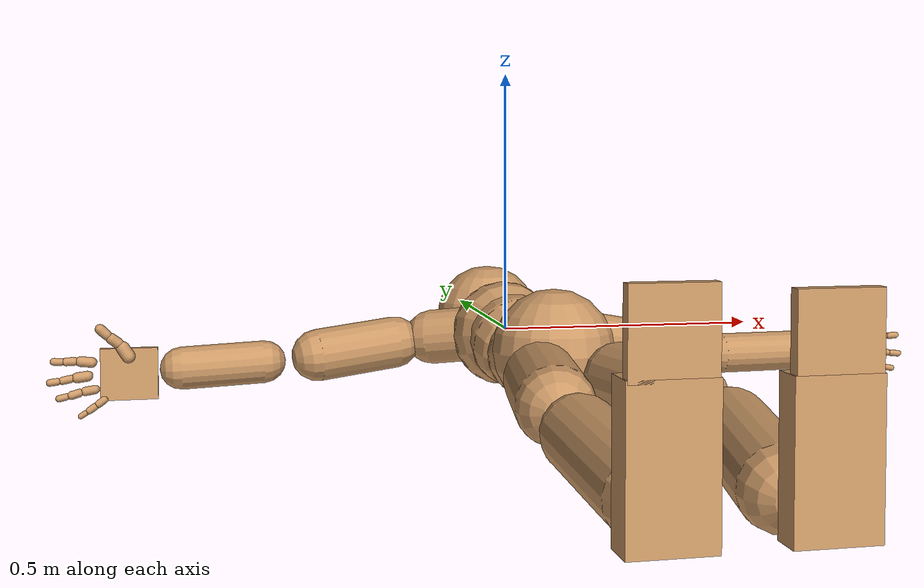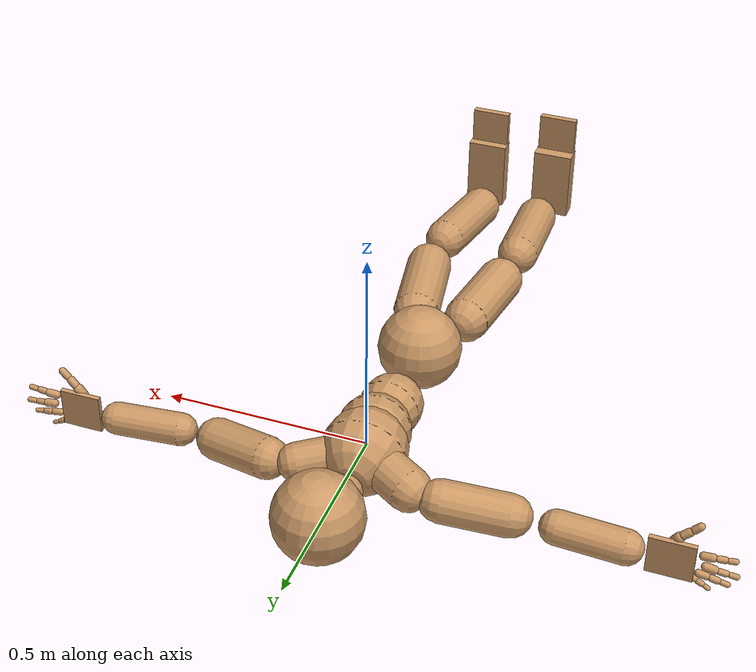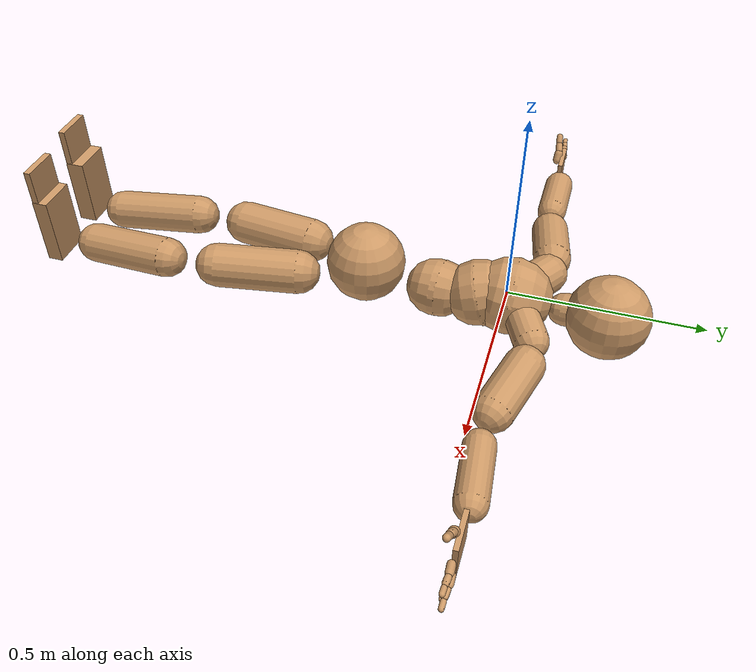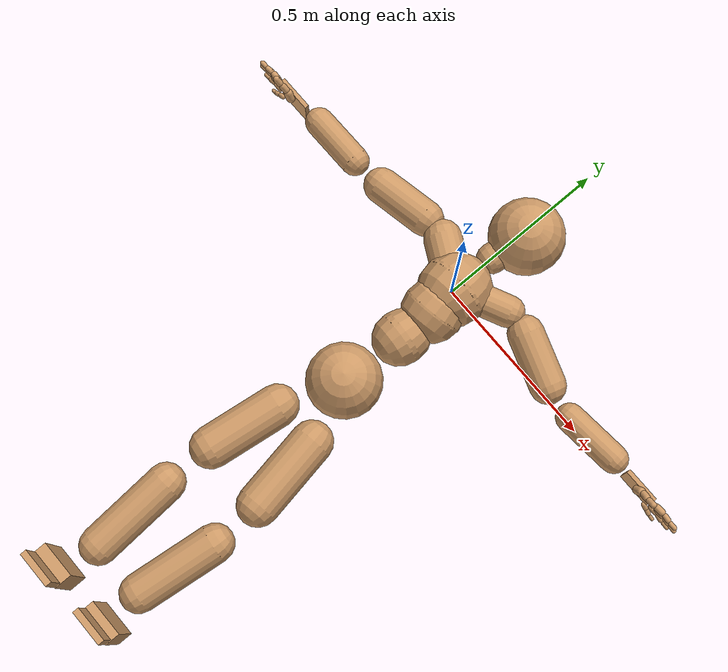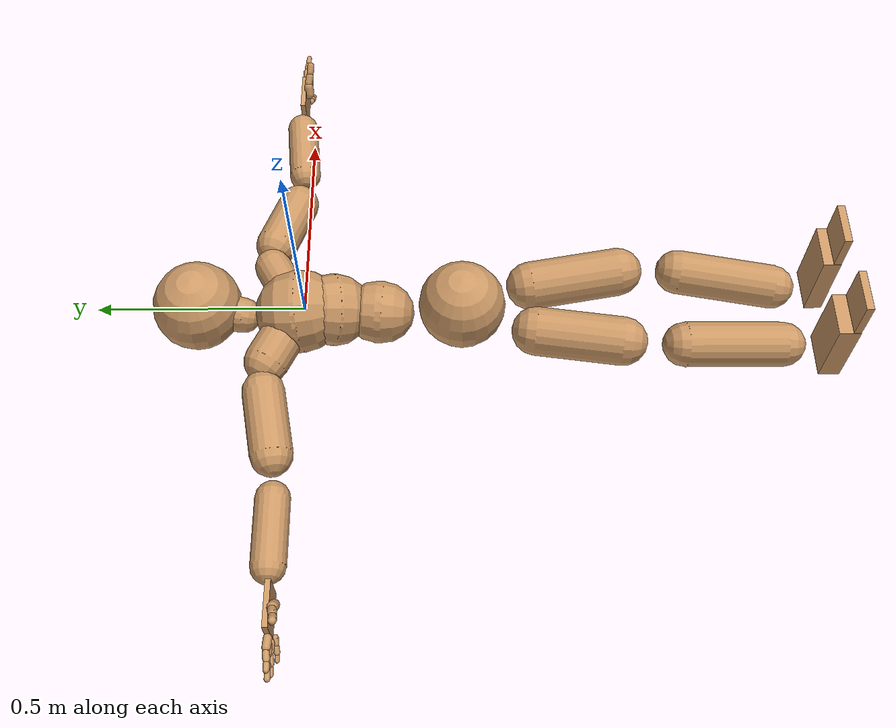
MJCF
<mujoco model="humanoid">
  <compiler coordinate="local" angle="degree"/>
  <default>
    <joint damping="0.0" armature="0.01" stiffness="0.0" limited="true"/>
    <geom conaffinity="1" condim="3" contype="7" margin="0.001" rgba="0.8 0.6 .4 1"/>
  </default>
  <asset>
    <texture type="skybox" builtin="gradient" rgb1=".4 .5 .6" rgb2="0 0 0" width="100" height="100"/>
    <texture builtin="flat" height="1278" mark="cross" markrgb="1 1 1" name="texgeom" random="0.01" rgb1="0.8 0.6 0.4" rgb2="0.8 0.6 0.4" type="cube" width="127"/>
    <texture builtin="checker" height="100" name="texplane" rgb1="0 0 0" rgb2="0.8 0.8 0.8" type="2d" width="100"/>
    <material name="MatPlane" reflectance="0.5" shininess="1" specular="1" texrepeat="60 60" texture="texplane"/>
    <material name="geom" texture="texgeom" texuniform="true"/>
  </asset>
  <worldbody>
    <body name="Pelvis" pos="0.0013 -0.38 0.0136">
      <freejoint name="Pelvis"/>
      <geom type="sphere" contype="1" conaffinity="1" density="4629.6296296296305" size="0.1049" pos="0.0000 0.0000 0.0000" name="Pelvis"/>
      <body name="L_Hip_x_link" pos="0.0549 -0.0969 -0.0231">
        <joint name="L_Hip_x" type="hinge" pos="0 0 0" axis="1 0 0" stiffness="800" damping="80" armature="0.02" range="-90.0000 90.0000"/>
        <inertial pos="0 0 0" mass="0.0001" diaginertia="1e-9 1e-9 1e-9"/>
        <body name="L_Hip_y_link" pos="0 0 0">
          <joint name="L_Hip_y" type="hinge" pos="0 0 0" axis="0 1 0" stiffness="800" damping="80" armature="0.02" range="-90.0000 90.0000"/>
          <inertial pos="0 0 0" mass="0.0001" diaginertia="1e-9 1e-9 1e-9"/>
          <body name="L_Hip" pos="0 0 0">
            <joint name="L_Hip_z" type="hinge" pos="0 0 0" axis="0 0 1" stiffness="800" damping="80" armature="0.02" range="-90.0000 90.0000"/>
            <geom type="capsule" contype="1" conaffinity="1" density="2040.816327" fromto="0.0127 -0.0722 0.0007 0.0506 -0.2888 0.0028" size="0.0591" name="L_Hip"/>
            <body name="L_Knee_x_link" pos="0.0633 -0.361 0.0035">
              <joint name="L_Knee_x" type="hinge" pos="0 0 0" axis="1 0 0" stiffness="800" damping="80" armature="0.02" range="-180.0000 180.0000"/>
              <inertial pos="0 0 0" mass="0.0001" diaginertia="1e-9 1e-9 1e-9"/>
              <body name="L_Knee_y_link" pos="0 0 0">
                <joint name="L_Knee_y" type="hinge" pos="0 0 0" axis="0 1 0" stiffness="800" damping="80" armature="0.02" range="-5.6250 5.6250"/>
                <inertial pos="0 0 0" mass="0.0001" diaginertia="1e-9 1e-9 1e-9"/>
                <body name="L_Knee" pos="0 0 0">
                  <joint name="L_Knee_z" type="hinge" pos="0 0 0" axis="0 0 1" stiffness="800" damping="80" armature="0.02" range="-5.6250 5.6250"/>
                  <geom type="capsule" contype="1" conaffinity="1" density="1234.567901" fromto="-0.0099 -0.0777 -0.0077 -0.0395 -0.3108 -0.0309" size="0.0544" name="L_Knee"/>
                  <body name="L_Ankle_x_link" pos="-0.0493 -0.3885 -0.0386">
                    <joint name="L_Ankle_x" type="hinge" pos="0 0 0" axis="1 0 0" stiffness="800" damping="80" armature="0.02" range="-90.0000 90.0000"/>
                    <inertial pos="0 0 0" mass="0.0001" diaginertia="1e-9 1e-9 1e-9"/>
                    <body name="L_Ankle_y_link" pos="0 0 0">
                      <joint name="L_Ankle_y" type="hinge" pos="0 0 0" axis="0 1 0" stiffness="800" damping="80" armature="0.02" range="-90.0000 90.0000"/>
                      <inertial pos="0 0 0" mass="0.0001" diaginertia="1e-9 1e-9 1e-9"/>
                      <body name="L_Ankle" pos="0 0 0">
                        <joint name="L_Ankle_z" type="hinge" pos="0 0 0" axis="0 0 1" stiffness="800" damping="80" armature="0.02" range="-90.0000 90.0000"/>
                        <geom type="box" contype="1" conaffinity="1" density="1000.000015" pos="0.0221 -0.0286 0.0672" size="0.053 0.0211 0.0945" quat="1.0000 0.0000 0.0000 0.0000" name="L_Ankle"/>
                        <body name="L_Toe_x_link" pos="0.0442 -0.0571 0.1344">
                          <joint name="L_Toe_x" type="hinge" pos="0 0 0" axis="1 0 0" stiffness="500" damping="50" armature="0.02" range="-90.0000 90.0000"/>
                          <inertial pos="0 0 0" mass="0.0001" diaginertia="1e-9 1e-9 1e-9"/>
                          <body name="L_Toe_y_link" pos="0 0 0">
                            <joint name="L_Toe_y" type="hinge" pos="0 0 0" axis="0 1 0" stiffness="500" damping="50" armature="0.02" range="-45.0000 45.0000"/>
                            <inertial pos="0 0 0" mass="0.0001" diaginertia="1e-9 1e-9 1e-9"/>
                            <body name="L_Toe" pos="0 0 0">
                              <joint name="L_Toe_z" type="hinge" pos="0 0 0" axis="0 0 1" stiffness="500" damping="50" armature="0.02" range="-45.0000 45.0000"/>
                              <geom type="box" contype="1" conaffinity="1" density="1000.000007" pos="-0.0221 0.0165 0.0682" size="0.0511 0.009 0.0525" quat="1.0000 0.0000 0.0000 0.0000" name="L_Toe"/>
                            </body>
                          </body>
                        </body>
                      </body>
                    </body>
                  </body>
                </body>
              </body>
            </body>
          </body>
        </body>
      </body>
      <body name="R_Hip_x_link" pos="-0.0564 -0.1082 -0.0163">
        <joint name="R_Hip_x" type="hinge" pos="0 0 0" axis="1 0 0" stiffness="800" damping="80" armature="0.02" range="-90.0000 90.0000"/>
        <inertial pos="0 0 0" mass="0.0001" diaginertia="1e-9 1e-9 1e-9"/>
        <body name="R_Hip_y_link" pos="0 0 0">
          <joint name="R_Hip_y" type="hinge" pos="0 0 0" axis="0 1 0" stiffness="800" damping="80" armature="0.02" range="-90.0000 90.0000"/>
          <inertial pos="0 0 0" mass="0.0001" diaginertia="1e-9 1e-9 1e-9"/>
          <body name="R_Hip" pos="0 0 0">
            <joint name="R_Hip_z" type="hinge" pos="0 0 0" axis="0 0 1" stiffness="800" damping="80" armature="0.02" range="-90.0000 90.0000"/>
            <geom type="capsule" contype="1" conaffinity="1" density="2040.816327" fromto="-0.0094 -0.0689 -0.0009 -0.0375 -0.2756 -0.0035" size="0.059" name="R_Hip"/>
            <body name="R_Knee_x_link" pos="-0.0468 -0.3445 -0.0044">
              <joint name="R_Knee_x" type="hinge" pos="0 0 0" axis="1 0 0" stiffness="800" damping="80" armature="0.02" range="-180.0000 180.0000"/>
              <inertial pos="0 0 0" mass="0.0001" diaginertia="1e-9 1e-9 1e-9"/>
              <body name="R_Knee_y_link" pos="0 0 0">
                <joint name="R_Knee_y" type="hinge" pos="0 0 0" axis="0 1 0" stiffness="800" damping="80" armature="0.02" range="-5.6250 5.6250"/>
                <inertial pos="0 0 0" mass="0.0001" diaginertia="1e-9 1e-9 1e-9"/>
                <body name="R_Knee" pos="0 0 0">
                  <joint name="R_Knee_z" type="hinge" pos="0 0 0" axis="0 0 1" stiffness="800" damping="80" armature="0.02" range="-5.6250 5.6250"/>
                  <geom type="capsule" contype="1" conaffinity="1" density="1234.567901" fromto="0.0039 -0.0801 -0.0074 0.0157 -0.3205 -0.0298" size="0.0541" name="R_Knee"/>
                  <body name="R_Ankle_x_link" pos="0.0196 -0.4006 -0.0372">
                    <joint name="R_Ankle_x" type="hinge" pos="0 0 0" axis="1 0 0" stiffness="800" damping="80" armature="0.02" range="-90.0000 90.0000"/>
                    <inertial pos="0 0 0" mass="0.0001" diaginertia="1e-9 1e-9 1e-9"/>
                    <body name="R_Ankle_y_link" pos="0 0 0">
                      <joint name="R_Ankle_y" type="hinge" pos="0 0 0" axis="0 1 0" stiffness="800" damping="80" armature="0.02" range="-90.0000 90.0000"/>
                      <inertial pos="0 0 0" mass="0.0001" diaginertia="1e-9 1e-9 1e-9"/>
                      <body name="R_Ankle" pos="0 0 0">
                        <joint name="R_Ankle_z" type="hinge" pos="0 0 0" axis="0 0 1" stiffness="800" damping="80" armature="0.02" range="-90.0000 90.0000"/>
                        <geom type="box" contype="1" conaffinity="1" density="999.999987" pos="-0.0172 -0.0282 0.0707" size="0.053 0.0252 0.0945" quat="1.0000 0.0000 0.0000 0.0000" name="R_Ankle"/>
                        <body name="R_Toe_x_link" pos="-0.0344 -0.0564 0.1413">
                          <joint name="R_Toe_x" type="hinge" pos="0 0 0" axis="1 0 0" stiffness="500" damping="50" armature="0.02" range="-90.0000 90.0000"/>
                          <inertial pos="0 0 0" mass="0.0001" diaginertia="1e-9 1e-9 1e-9"/>
                          <body name="R_Toe_y_link" pos="0 0 0">
                            <joint name="R_Toe_y" type="hinge" pos="0 0 0" axis="0 1 0" stiffness="500" damping="50" armature="0.02" range="-45.0000 45.0000"/>
                            <inertial pos="0 0 0" mass="0.0001" diaginertia="1e-9 1e-9 1e-9"/>
                            <body name="R_Toe" pos="0 0 0">
                              <joint name="R_Toe_z" type="hinge" pos="0 0 0" axis="0 0 1" stiffness="500" damping="50" armature="0.02" range="-45.0000 45.0000"/>
                              <geom type="box" contype="1" conaffinity="1" density="1000.000005" pos="0.0172 0.0118 0.0717" size="0.0511 0.0088 0.0525" quat="1.0000 0.0000 0.0000 0.0000" name="R_Toe"/>
                            </body>
                          </body>
                        </body>
                      </body>
                    </body>
                  </body>
                </body>
              </body>
            </body>
          </body>
        </body>
      </body>
      <body name="Torso_x_link" pos="-0.0026 0.1184 -0.0391">
        <joint name="Torso_x" type="hinge" pos="0 0 0" axis="1 0 0" stiffness="1000" damping="100" armature="0.02" range="-60.0000 60.0000"/>
        <inertial pos="0 0 0" mass="0.0001" diaginertia="1e-9 1e-9 1e-9"/>
        <body name="Torso_y_link" pos="0 0 0">
          <joint name="Torso_y" type="hinge" pos="0 0 0" axis="0 1 0" stiffness="1000" damping="100" armature="0.02" range="-60.0000 60.0000"/>
          <inertial pos="0 0 0" mass="0.0001" diaginertia="1e-9 1e-9 1e-9"/>
          <body name="Torso" pos="0 0 0">
            <joint name="Torso_z" type="hinge" pos="0 0 0" axis="0 0 1" stiffness="1000" damping="100" armature="0.02" range="-60.0000 60.0000"/>
            <geom type="capsule" contype="1" conaffinity="1" density="2040.816327" fromto="0.0053 0.0733 0.0010 0.0065 0.0896 0.0012" size="0.0759" name="Torso"/>
            <body name="Spine_x_link" pos="0.0118 0.1628 0.0022">
              <joint name="Spine_x" type="hinge" pos="0 0 0" axis="1 0 0" stiffness="1000" damping="100" armature="0.02" range="-60.0000 60.0000"/>
              <inertial pos="0 0 0" mass="0.0001" diaginertia="1e-9 1e-9 1e-9"/>
              <body name="Spine_y_link" pos="0 0 0">
                <joint name="Spine_y" type="hinge" pos="0 0 0" axis="0 1 0" stiffness="1000" damping="100" armature="0.02" range="-60.0000 60.0000"/>
                <inertial pos="0 0 0" mass="0.0001" diaginertia="1e-9 1e-9 1e-9"/>
                <body name="Spine" pos="0 0 0">
                  <joint name="Spine_z" type="hinge" pos="0 0 0" axis="0 0 1" stiffness="1000" damping="100" armature="0.02" range="-60.0000 60.0000"/>
                  <geom type="capsule" contype="1" conaffinity="1" density="2040.816327" fromto="-0.0043 0.0272 0.0088 -0.0053 0.0332 0.0107" size="0.0883" name="Spine"/>
                  <body name="Chest_x_link" pos="-0.0096 0.0604 0.0195">
                    <joint name="Chest_x" type="hinge" pos="0 0 0" axis="1 0 0" stiffness="1000" damping="100" armature="0.02" range="-60.0000 60.0000"/>
                    <inertial pos="0 0 0" mass="0.0001" diaginertia="1e-9 1e-9 1e-9"/>
                    <body name="Chest_y_link" pos="0 0 0">
                      <joint name="Chest_y" type="hinge" pos="0 0 0" axis="0 1 0" stiffness="1000" damping="100" armature="0.02" range="-60.0000 60.0000"/>
                      <inertial pos="0 0 0" mass="0.0001" diaginertia="1e-9 1e-9 1e-9"/>
                      <body name="Chest" pos="0 0 0">
                        <joint name="Chest_z" type="hinge" pos="0 0 0" axis="0 0 1" stiffness="1000" damping="100" armature="0.02" range="-60.0000 60.0000"/>
                        <geom type="capsule" contype="1" conaffinity="1" density="2040.816327" fromto="-0.0018 0.0470 -0.0052 -0.0022 0.0574 -0.0064" size="0.1014" name="Chest"/>
                        <body name="Neck_x_link" pos="-0.0086 0.162 -0.023">
                          <joint name="Neck_x" type="hinge" pos="0 0 0" axis="1 0 0" stiffness="500" damping="50" armature="0.02" range="-180.0000 180.0000"/>
                          <inertial pos="0 0 0" mass="0.0001" diaginertia="1e-9 1e-9 1e-9"/>
                          <body name="Neck_y_link" pos="0 0 0">
                            <joint name="Neck_y" type="hinge" pos="0 0 0" axis="0 1 0" stiffness="500" damping="50" armature="0.02" range="-180.0000 180.0000"/>
                            <inertial pos="0 0 0" mass="0.0001" diaginertia="1e-9 1e-9 1e-9"/>
                            <body name="Neck" pos="0 0 0">
                              <joint name="Neck_z" type="hinge" pos="0 0 0" axis="0 0 1" stiffness="500" damping="50" armature="0.02" range="-180.0000 180.0000"/>
                              <geom type="capsule" contype="1" conaffinity="1" density="1000" fromto="0.0045 0.0277 0.0041 0.0181 0.1108 0.0165" size="0.0429" name="Neck"/>
                              <body name="Head_x_link" pos="0.0226 0.1385 0.0206">
                                <joint name="Head_x" type="hinge" pos="0 0 0" axis="1 0 0" stiffness="500" damping="50" armature="0.02" range="-90.0000 90.0000"/>
                                <inertial pos="0 0 0" mass="0.0001" diaginertia="1e-9 1e-9 1e-9"/>
                                <body name="Head_y_link" pos="0 0 0">
                                  <joint name="Head_y" type="hinge" pos="0 0 0" axis="0 1 0" stiffness="500" damping="50" armature="0.02" range="-90.0000 90.0000"/>
                                  <inertial pos="0 0 0" mass="0.0001" diaginertia="1e-9 1e-9 1e-9"/>
                                  <body name="Head" pos="0 0 0">
                                    <joint name="Head_z" type="hinge" pos="0 0 0" axis="0 0 1" stiffness="500" damping="50" armature="0.02" range="-90.0000 90.0000"/>
                                    <geom type="sphere" contype="1" conaffinity="1" density="1000" size="0.1076" pos="0.0000 0.0000 0.0000" name="Head"/>
                                  </body>
                                </body>
                              </body>
                            </body>
                          </body>
                        </body>
                        <body name="L_Thorax_x_link" pos="0.0379 0.0752 -0.004">
                          <joint name="L_Thorax_x" type="hinge" pos="0 0 0" axis="1 0 0" stiffness="500" damping="50" armature="0.02" range="-180.0000 180.0000"/>
                          <inertial pos="0 0 0" mass="0.0001" diaginertia="1e-9 1e-9 1e-9"/>
                          <body name="L_Thorax_y_link" pos="0 0 0">
                            <joint name="L_Thorax_y" type="hinge" pos="0 0 0" axis="0 1 0" stiffness="500" damping="50" armature="0.02" range="-180.0000 180.0000"/>
                            <inertial pos="0 0 0" mass="0.0001" diaginertia="1e-9 1e-9 1e-9"/>
                            <body name="L_Thorax" pos="0 0 0">
                              <joint name="L_Thorax_z" type="hinge" pos="0 0 0" axis="0 0 1" stiffness="500" damping="50" armature="0.02" range="-180.0000 180.0000"/>
                              <geom type="capsule" contype="1" conaffinity="1" density="1000" fromto="0.0250 0.0131 -0.0042 0.1001 0.0524 -0.0168" size="0.0455" name="L_Thorax"/>
                              <body name="L_Shoulder_x_link" pos="0.1251 0.0655 -0.021">
                                <joint name="L_Shoulder_x" type="hinge" pos="0 0 0" axis="1 0 0" stiffness="500" damping="50" armature="0.02" range="-180.0000 180.0000"/>
                                <inertial pos="0 0 0" mass="0.0001" diaginertia="1e-9 1e-9 1e-9"/>
                                <body name="L_Shoulder_y_link" pos="0 0 0">
                                  <joint name="L_Shoulder_y" type="hinge" pos="0 0 0" axis="0 1 0" stiffness="500" damping="50" armature="0.02" range="-180.0000 180.0000"/>
                                  <inertial pos="0 0 0" mass="0.0001" diaginertia="1e-9 1e-9 1e-9"/>
                                  <body name="L_Shoulder" pos="0 0 0">
                                    <joint name="L_Shoulder_z" type="hinge" pos="0 0 0" axis="0 0 1" stiffness="500" damping="50" armature="0.02" range="-180.0000 180.0000"/>
                                    <geom type="capsule" contype="1" conaffinity="1" density="1000" fromto="0.0489 -0.0152 -0.0078 0.1957 -0.0610 -0.0310" size="0.0516" name="L_Shoulder"/>
                                    <body name="L_Elbow_x_link" pos="0.2447 -0.0762 -0.0388">
                                      <joint name="L_Elbow_x" type="hinge" pos="0 0 0" axis="1 0 0" stiffness="500" damping="50" armature="0.02" range="-180.0000 180.0000"/>
                                      <inertial pos="0 0 0" mass="0.0001" diaginertia="1e-9 1e-9 1e-9"/>
                                      <body name="L_Elbow_y_link" pos="0 0 0">
                                        <joint name="L_Elbow_y" type="hinge" pos="0 0 0" axis="0 1 0" stiffness="500" damping="50" armature="0.02" range="-180.0000 180.0000"/>
                                        <inertial pos="0 0 0" mass="0.0001" diaginertia="1e-9 1e-9 1e-9"/>
                                        <body name="L_Elbow" pos="0 0 0">
                                          <joint name="L_Elbow_z" type="hinge" pos="0 0 0" axis="0 0 1" stiffness="500" damping="50" armature="0.02" range="-180.0000 180.0000"/>
                                          <geom type="capsule" contype="1" conaffinity="1" density="1000" fromto="0.0537 0.0049 -0.0003 0.2149 0.0198 -0.0013" size="0.0403" name="L_Elbow"/>
                                          <body name="L_Wrist_x_link" pos="0.2686 0.0247 -0.0016">
                                            <joint name="L_Wrist_x" type="hinge" pos="0 0 0" axis="1 0 0" stiffness="300" damping="30" armature="0.02" range="-180.0000 180.0000"/>
                                            <inertial pos="0 0 0" mass="0.0001" diaginertia="1e-9 1e-9 1e-9"/>
                                            <body name="L_Wrist_y_link" pos="0 0 0">
                                              <joint name="L_Wrist_y" type="hinge" pos="0 0 0" axis="0 1 0" stiffness="300" damping="30" armature="0.02" range="-180.0000 180.0000"/>
                                              <inertial pos="0 0 0" mass="0.0001" diaginertia="1e-9 1e-9 1e-9"/>
                                              <body name="L_Wrist" pos="0 0 0">
                                                <joint name="L_Wrist_z" type="hinge" pos="0 0 0" axis="0 0 1" stiffness="300" damping="30" armature="0.02" range="-180.0000 180.0000"/>
                                                <geom type="box" contype="1" conaffinity="1" density="2541.499907" pos="0.0456 -0.0061 -0.0030" size="0.0516 0.0062 0.0494" quat="1.0000 0.0000 0.0000 0.0000" name="L_Wrist"/>
                                                <body name="L_Index1_x_link" pos="0.1073 -0.0096 0.0213">
                                                  <joint name="L_Index1_x" type="hinge" pos="0 0 0" axis="1 0 0" stiffness="100" damping="10" armature="0.02" range="-180.0000 180.0000"/>
                                                  <inertial pos="0 0 0" mass="0.0001" diaginertia="1e-9 1e-9 1e-9"/>
                                                  <body name="L_Index1_y_link" pos="0 0 0">
                                                    <joint name="L_Index1_y" type="hinge" pos="0 0 0" axis="0 1 0" stiffness="100" damping="10" armature="0.02" range="-180.0000 180.0000"/>
                                                    <inertial pos="0 0 0" mass="0.0001" diaginertia="1e-9 1e-9 1e-9"/>
                                                    <body name="L_Index1" pos="0 0 0">
                                                      <joint name="L_Index1_z" type="hinge" pos="0 0 0" axis="0 0 1" stiffness="100" damping="10" armature="0.02" range="-180.0000 180.0000"/>
                                                      <geom type="capsule" contype="1" conaffinity="1" density="1000" fromto="0.0068 0.0003 0.0008 0.0271 0.0013 0.0030" size="0.0097" name="L_Index1"/>
                                                      <body name="L_Index2_x_link" pos="0.0339 0.0016 0.0038">
                                                        <joint name="L_Index2_x" type="hinge" pos="0 0 0" axis="1 0 0" stiffness="100" damping="10" armature="0.02" range="-180.0000 180.0000"/>
                                                        <inertial pos="0 0 0" mass="0.0001" diaginertia="1e-9 1e-9 1e-9"/>
                                                        <body name="L_Index2_y_link" pos="0 0 0">
                                                          <joint name="L_Index2_y" type="hinge" pos="0 0 0" axis="0 1 0" stiffness="100" damping="10" armature="0.02" range="-180.0000 180.0000"/>
                                                          <inertial pos="0 0 0" mass="0.0001" diaginertia="1e-9 1e-9 1e-9"/>
                                                          <body name="L_Index2" pos="0 0 0">
                                                            <joint name="L_Index2_z" type="hinge" pos="0 0 0" axis="0 0 1" stiffness="100" damping="10" armature="0.02" range="-180.0000 180.0000"/>
                                                            <geom type="capsule" contype="1" conaffinity="1" density="1000" fromto="0.0048 -0.0006 -0.0001 0.0190 -0.0023 -0.0003" size="0.0079" name="L_Index2"/>
                                                            <body name="L_Index3_x_link" pos="0.0238 -0.0028 -0.0004">
                                                            <joint name="L_Index3_x" type="hinge" pos="0 0 0" axis="1 0 0" stiffness="100" damping="10" armature="0.02" range="-180.0000 180.0000"/>
                                                            <inertial pos="0 0 0" mass="0.0001" diaginertia="1e-9 1e-9 1e-9"/>
                                                            <body name="L_Index3_y_link" pos="0 0 0">
                                                            <joint name="L_Index3_y" type="hinge" pos="0 0 0" axis="0 1 0" stiffness="100" damping="10" armature="0.02" range="-180.0000 180.0000"/>
                                                            <inertial pos="0 0 0" mass="0.0001" diaginertia="1e-9 1e-9 1e-9"/>
                                                            <body name="L_Index3" pos="0 0 0">
                                                            <joint name="L_Index3_z" type="hinge" pos="0 0 0" axis="0 0 1" stiffness="100" damping="10" armature="0.02" range="-180.0000 180.0000"/>
                                                            <geom type="capsule" contype="1" conaffinity="1" density="1000" fromto="0.0052 -0.0002 0.0003 0.0206 -0.0007 0.0013" size="0.0067" name="L_Index3"/>
                                                            </body>
                                                            </body>
                                                            </body>
                                                          </body>
                                                        </body>
                                                      </body>
                                                    </body>
                                                  </body>
                                                </body>
                                                <body name="L_Middle1_x_link" pos="0.1154 -0.0066 -0.0034">
                                                  <joint name="L_Middle1_x" type="hinge" pos="0 0 0" axis="1 0 0" stiffness="100" damping="10" armature="0.02" range="-180.0000 180.0000"/>
                                                  <inertial pos="0 0 0" mass="0.0001" diaginertia="1e-9 1e-9 1e-9"/>
                                                  <body name="L_Middle1_y_link" pos="0 0 0">
                                                    <joint name="L_Middle1_y" type="hinge" pos="0 0 0" axis="0 1 0" stiffness="100" damping="10" armature="0.02" range="-180.0000 180.0000"/>
                                                    <inertial pos="0 0 0" mass="0.0001" diaginertia="1e-9 1e-9 1e-9"/>
                                                    <body name="L_Middle1" pos="0 0 0">
                                                      <joint name="L_Middle1_z" type="hinge" pos="0 0 0" axis="0 0 1" stiffness="100" damping="10" armature="0.02" range="-180.0000 180.0000"/>
                                                      <geom type="capsule" contype="1" conaffinity="1" density="1000" fromto="0.0065 0.0001 -0.0008 0.0258 0.0004 -0.0034" size="0.01" name="L_Middle1"/>
                                                      <body name="L_Middle2_x_link" pos="0.0323 0.0005 -0.0042">
                                                        <joint name="L_Middle2_x" type="hinge" pos="0 0 0" axis="1 0 0" stiffness="100" damping="10" armature="0.02" range="-180.0000 180.0000"/>
                                                        <inertial pos="0 0 0" mass="0.0001" diaginertia="1e-9 1e-9 1e-9"/>
                                                        <body name="L_Middle2_y_link" pos="0 0 0">
                                                          <joint name="L_Middle2_y" type="hinge" pos="0 0 0" axis="0 1 0" stiffness="100" damping="10" armature="0.02" range="-180.0000 180.0000"/>
                                                          <inertial pos="0 0 0" mass="0.0001" diaginertia="1e-9 1e-9 1e-9"/>
                                                          <body name="L_Middle2" pos="0 0 0">
                                                            <joint name="L_Middle2_z" type="hinge" pos="0 0 0" axis="0 0 1" stiffness="100" damping="10" armature="0.02" range="-180.0000 180.0000"/>
                                                            <geom type="capsule" contype="1" conaffinity="1" density="1000" fromto="0.0049 -0.0005 -0.0009 0.0197 -0.0020 -0.0036" size="0.0074" name="L_Middle2"/>
                                                            <body name="L_Middle3_x_link" pos="0.0246 -0.0025 -0.0045">
                                                            <joint name="L_Middle3_x" type="hinge" pos="0 0 0" axis="1 0 0" stiffness="100" damping="10" armature="0.02" range="-180.0000 180.0000"/>
                                                            <inertial pos="0 0 0" mass="0.0001" diaginertia="1e-9 1e-9 1e-9"/>
                                                            <body name="L_Middle3_y_link" pos="0 0 0">
                                                            <joint name="L_Middle3_y" type="hinge" pos="0 0 0" axis="0 1 0" stiffness="100" damping="10" armature="0.02" range="-180.0000 180.0000"/>
                                                            <inertial pos="0 0 0" mass="0.0001" diaginertia="1e-9 1e-9 1e-9"/>
                                                            <body name="L_Middle3" pos="0 0 0">
                                                            <joint name="L_Middle3_z" type="hinge" pos="0 0 0" axis="0 0 1" stiffness="100" damping="10" armature="0.02" range="-180.0000 180.0000"/>
                                                            <geom type="capsule" contype="1" conaffinity="1" density="1000" fromto="0.0053 -0.0001 -0.0005 0.0213 -0.0004 -0.0020" size="0.0066" name="L_Middle3"/>
                                                            </body>
                                                            </body>
                                                            </body>
                                                          </body>
                                                        </body>
                                                      </body>
                                                    </body>
                                                  </body>
                                                </body>
                                                <body name="L_Pinky1_x_link" pos="0.0884 -0.0152 -0.0469">
                                                  <joint name="L_Pinky1_x" type="hinge" pos="0 0 0" axis="1 0 0" stiffness="100" damping="10" armature="0.02" range="-180.0000 180.0000"/>
                                                  <inertial pos="0 0 0" mass="0.0001" diaginertia="1e-9 1e-9 1e-9"/>
                                                  <body name="L_Pinky1_y_link" pos="0 0 0">
                                                    <joint name="L_Pinky1_y" type="hinge" pos="0 0 0" axis="0 1 0" stiffness="100" damping="10" armature="0.02" range="-180.0000 180.0000"/>
                                                    <inertial pos="0 0 0" mass="0.0001" diaginertia="1e-9 1e-9 1e-9"/>
                                                    <body name="L_Pinky1" pos="0 0 0">
                                                      <joint name="L_Pinky1_z" type="hinge" pos="0 0 0" axis="0 0 1" stiffness="100" damping="10" armature="0.02" range="-180.0000 180.0000"/>
                                                      <geom type="capsule" contype="1" conaffinity="1" density="1000" fromto="0.0034 -0.0004 -0.0024 0.0137 -0.0015 -0.0097" size="0.0072" name="L_Pinky1"/>
                                                      <body name="L_Pinky2_x_link" pos="0.0171 -0.0019 -0.0121">
                                                        <joint name="L_Pinky2_x" type="hinge" pos="0 0 0" axis="1 0 0" stiffness="100" damping="10" armature="0.02" range="-180.0000 180.0000"/>
                                                        <inertial pos="0 0 0" mass="0.0001" diaginertia="1e-9 1e-9 1e-9"/>
                                                        <body name="L_Pinky2_y_link" pos="0 0 0">
                                                          <joint name="L_Pinky2_y" type="hinge" pos="0 0 0" axis="0 1 0" stiffness="100" damping="10" armature="0.02" range="-180.0000 180.0000"/>
                                                          <inertial pos="0 0 0" mass="0.0001" diaginertia="1e-9 1e-9 1e-9"/>
                                                          <body name="L_Pinky2" pos="0 0 0">
                                                            <joint name="L_Pinky2_z" type="hinge" pos="0 0 0" axis="0 0 1" stiffness="100" damping="10" armature="0.02" range="-180.0000 180.0000"/>
                                                            <geom type="capsule" contype="1" conaffinity="1" density="1000" fromto="0.0034 -0.0004 -0.0023 0.0134 -0.0017 -0.0091" size="0.0068" name="L_Pinky2"/>
                                                            <body name="L_Pinky3_x_link" pos="0.0168 -0.0022 -0.0113">
                                                            <joint name="L_Pinky3_x" type="hinge" pos="0 0 0" axis="1 0 0" stiffness="100" damping="10" armature="0.02" range="-180.0000 180.0000"/>
                                                            <inertial pos="0 0 0" mass="0.0001" diaginertia="1e-9 1e-9 1e-9"/>
                                                            <body name="L_Pinky3_y_link" pos="0 0 0">
                                                            <joint name="L_Pinky3_y" type="hinge" pos="0 0 0" axis="0 1 0" stiffness="100" damping="10" armature="0.02" range="-180.0000 180.0000"/>
                                                            <inertial pos="0 0 0" mass="0.0001" diaginertia="1e-9 1e-9 1e-9"/>
                                                            <body name="L_Pinky3" pos="0 0 0">
                                                            <joint name="L_Pinky3_z" type="hinge" pos="0 0 0" axis="0 0 1" stiffness="100" damping="10" armature="0.02" range="-180.0000 180.0000"/>
                                                            <geom type="capsule" contype="1" conaffinity="1" density="1000" fromto="0.0038 -0.0000 -0.0019 0.0150 -0.0001 -0.0075" size="0.0052" name="L_Pinky3"/>
                                                            </body>
                                                            </body>
                                                            </body>
                                                          </body>
                                                        </body>
                                                      </body>
                                                    </body>
                                                  </body>
                                                </body>
                                                <body name="L_Ring1_x_link" pos="0.1026 -0.0094 -0.0289">
                                                  <joint name="L_Ring1_x" type="hinge" pos="0 0 0" axis="1 0 0" stiffness="100" damping="10" armature="0.02" range="-180.0000 180.0000"/>
                                                  <inertial pos="0 0 0" mass="0.0001" diaginertia="1e-9 1e-9 1e-9"/>
                                                  <body name="L_Ring1_y_link" pos="0 0 0">
                                                    <joint name="L_Ring1_y" type="hinge" pos="0 0 0" axis="0 1 0" stiffness="100" damping="10" armature="0.02" range="-180.0000 180.0000"/>
                                                    <inertial pos="0 0 0" mass="0.0001" diaginertia="1e-9 1e-9 1e-9"/>
                                                    <body name="L_Ring1" pos="0 0 0">
                                                      <joint name="L_Ring1_z" type="hinge" pos="0 0 0" axis="0 0 1" stiffness="100" damping="10" armature="0.02" range="-180.0000 180.0000"/>
                                                      <geom type="capsule" contype="1" conaffinity="1" density="1000" fromto="0.0060 0.0002 -0.0010 0.0239 0.0006 -0.0040" size="0.0085" name="L_Ring1"/>
                                                      <body name="L_Ring2_x_link" pos="0.0298 0.0008 -0.005">
                                                        <joint name="L_Ring2_x" type="hinge" pos="0 0 0" axis="1 0 0" stiffness="100" damping="10" armature="0.02" range="-180.0000 180.0000"/>
                                                        <inertial pos="0 0 0" mass="0.0001" diaginertia="1e-9 1e-9 1e-9"/>
                                                        <body name="L_Ring2_y_link" pos="0 0 0">
                                                          <joint name="L_Ring2_y" type="hinge" pos="0 0 0" axis="0 1 0" stiffness="100" damping="10" armature="0.02" range="-180.0000 180.0000"/>
                                                          <inertial pos="0 0 0" mass="0.0001" diaginertia="1e-9 1e-9 1e-9"/>
                                                          <body name="L_Ring2" pos="0 0 0">
                                                            <joint name="L_Ring2_z" type="hinge" pos="0 0 0" axis="0 0 1" stiffness="100" damping="10" armature="0.02" range="-180.0000 180.0000"/>
                                                            <geom type="capsule" contype="1" conaffinity="1" density="1000" fromto="0.0048 -0.0004 -0.0014 0.0192 -0.0018 -0.0055" size="0.0079" name="L_Ring2"/>
                                                            <body name="L_Ring3_x_link" pos="0.024 -0.0022 -0.0068">
                                                            <joint name="L_Ring3_x" type="hinge" pos="0 0 0" axis="1 0 0" stiffness="100" damping="10" armature="0.02" range="-180.0000 180.0000"/>
                                                            <inertial pos="0 0 0" mass="0.0001" diaginertia="1e-9 1e-9 1e-9"/>
                                                            <body name="L_Ring3_y_link" pos="0 0 0">
                                                            <joint name="L_Ring3_y" type="hinge" pos="0 0 0" axis="0 1 0" stiffness="100" damping="10" armature="0.02" range="-180.0000 180.0000"/>
                                                            <inertial pos="0 0 0" mass="0.0001" diaginertia="1e-9 1e-9 1e-9"/>
                                                            <body name="L_Ring3" pos="0 0 0">
                                                            <joint name="L_Ring3_z" type="hinge" pos="0 0 0" axis="0 0 1" stiffness="100" damping="10" armature="0.02" range="-180.0000 180.0000"/>
                                                            <geom type="capsule" contype="1" conaffinity="1" density="1000" fromto="0.0052 -0.0000 -0.0010 0.0208 -0.0002 -0.0039" size="0.0061" name="L_Ring3"/>
                                                            </body>
                                                            </body>
                                                            </body>
                                                          </body>
                                                        </body>
                                                      </body>
                                                    </body>
                                                  </body>
                                                </body>
                                                <body name="L_Thumb1_x_link" pos="0.0425 -0.0203 0.0275">
                                                  <joint name="L_Thumb1_x" type="hinge" pos="0 0 0" axis="1 0 0" stiffness="100" damping="10" armature="0.02" range="-180.0000 180.0000"/>
                                                  <inertial pos="0 0 0" mass="0.0001" diaginertia="1e-9 1e-9 1e-9"/>
                                                  <body name="L_Thumb1_y_link" pos="0 0 0">
                                                    <joint name="L_Thumb1_y" type="hinge" pos="0 0 0" axis="0 1 0" stiffness="100" damping="10" armature="0.02" range="-180.0000 180.0000"/>
                                                    <inertial pos="0 0 0" mass="0.0001" diaginertia="1e-9 1e-9 1e-9"/>
                                                    <body name="L_Thumb1" pos="0 0 0">
                                                      <joint name="L_Thumb1_z" type="hinge" pos="0 0 0" axis="0 0 1" stiffness="100" damping="10" armature="0.02" range="-180.0000 180.0000"/>
                                                      <geom type="capsule" contype="1" conaffinity="1" density="1000" fromto="0.0035 0.0004 0.0054 0.0141 0.0014 0.0217" size="0.0127" name="L_Thumb1"/>
                                                      <body name="L_Thumb2_x_link" pos="0.0176 0.0018 0.0271">
                                                        <joint name="L_Thumb2_x" type="hinge" pos="0 0 0" axis="1 0 0" stiffness="100" damping="10" armature="0.02" range="-180.0000 180.0000"/>
                                                        <inertial pos="0 0 0" mass="0.0001" diaginertia="1e-9 1e-9 1e-9"/>
                                                        <body name="L_Thumb2_y_link" pos="0 0 0">
                                                          <joint name="L_Thumb2_y" type="hinge" pos="0 0 0" axis="0 1 0" stiffness="100" damping="10" armature="0.02" range="-180.0000 180.0000"/>
                                                          <inertial pos="0 0 0" mass="0.0001" diaginertia="1e-9 1e-9 1e-9"/>
                                                          <body name="L_Thumb2" pos="0 0 0">
                                                            <joint name="L_Thumb2_z" type="hinge" pos="0 0 0" axis="0 0 1" stiffness="100" damping="10" armature="0.02" range="-180.0000 180.0000"/>
                                                            <geom type="capsule" contype="1" conaffinity="1" density="1000" fromto="0.0042 -0.0010 0.0034 0.0170 -0.0040 0.0137" size="0.0101" name="L_Thumb2"/>
                                                            <body name="L_Thumb3_x_link" pos="0.0212 -0.005 0.0171">
                                                            <joint name="L_Thumb3_x" type="hinge" pos="0 0 0" axis="1 0 0" stiffness="100" damping="10" armature="0.02" range="-180.0000 180.0000"/>
                                                            <inertial pos="0 0 0" mass="0.0001" diaginertia="1e-9 1e-9 1e-9"/>
                                                            <body name="L_Thumb3_y_link" pos="0 0 0">
                                                            <joint name="L_Thumb3_y" type="hinge" pos="0 0 0" axis="0 1 0" stiffness="100" damping="10" armature="0.02" range="-180.0000 180.0000"/>
                                                            <inertial pos="0 0 0" mass="0.0001" diaginertia="1e-9 1e-9 1e-9"/>
                                                            <body name="L_Thumb3" pos="0 0 0">
                                                            <joint name="L_Thumb3_z" type="hinge" pos="0 0 0" axis="0 0 1" stiffness="100" damping="10" armature="0.02" range="-180.0000 180.0000"/>
                                                            <geom type="capsule" contype="1" conaffinity="1" density="1000" fromto="0.0046 -0.0006 0.0038 0.0186 -0.0024 0.0153" size="0.0091" name="L_Thumb3"/>
                                                            </body>
                                                            </body>
                                                            </body>
                                                          </body>
                                                        </body>
                                                      </body>
                                                    </body>
                                                  </body>
                                                </body>
                                              </body>
                                            </body>
                                          </body>
                                        </body>
                                      </body>
                                    </body>
                                  </body>
                                </body>
                              </body>
                            </body>
                          </body>
                        </body>
                        <body name="R_Thorax_x_link" pos="-0.0411 0.0761 -0.0077">
                          <joint name="R_Thorax_x" type="hinge" pos="0 0 0" axis="1 0 0" stiffness="500" damping="50" armature="0.02" range="-180.0000 180.0000"/>
                          <inertial pos="0 0 0" mass="0.0001" diaginertia="1e-9 1e-9 1e-9"/>
                          <body name="R_Thorax_y_link" pos="0 0 0">
                            <joint name="R_Thorax_y" type="hinge" pos="0 0 0" axis="0 1 0" stiffness="500" damping="50" armature="0.02" range="-180.0000 180.0000"/>
                            <inertial pos="0 0 0" mass="0.0001" diaginertia="1e-9 1e-9 1e-9"/>
                            <body name="R_Thorax" pos="0 0 0">
                              <joint name="R_Thorax_z" type="hinge" pos="0 0 0" axis="0 0 1" stiffness="500" damping="50" armature="0.02" range="-180.0000 180.0000"/>
                              <geom type="capsule" contype="1" conaffinity="1" density="1000" fromto="-0.0232 0.0124 -0.0031 -0.0930 0.0495 -0.0124" size="0.054" name="R_Thorax"/>
                              <body name="R_Shoulder_x_link" pos="-0.1162 0.0619 -0.0155">
                                <joint name="R_Shoulder_x" type="hinge" pos="0 0 0" axis="1 0 0" stiffness="500" damping="50" armature="0.02" range="-180.0000 180.0000"/>
                                <inertial pos="0 0 0" mass="0.0001" diaginertia="1e-9 1e-9 1e-9"/>
                                <body name="R_Shoulder_y_link" pos="0 0 0">
                                  <joint name="R_Shoulder_y" type="hinge" pos="0 0 0" axis="0 1 0" stiffness="500" damping="50" armature="0.02" range="-180.0000 180.0000"/>
                                  <inertial pos="0 0 0" mass="0.0001" diaginertia="1e-9 1e-9 1e-9"/>
                                  <body name="R_Shoulder" pos="0 0 0">
                                    <joint name="R_Shoulder_z" type="hinge" pos="0 0 0" axis="0 0 1" stiffness="500" damping="50" armature="0.02" range="-180.0000 180.0000"/>
                                    <geom type="capsule" contype="1" conaffinity="1" density="1000" fromto="-0.0522 -0.0091 -0.0058 -0.2088 -0.0365 -0.0232" size="0.0509" name="R_Shoulder"/>
                                    <body name="R_Elbow_x_link" pos="-0.261 -0.0456 -0.029">
                                      <joint name="R_Elbow_x" type="hinge" pos="0 0 0" axis="1 0 0" stiffness="500" damping="50" armature="0.02" range="-180.0000 180.0000"/>
                                      <inertial pos="0 0 0" mass="0.0001" diaginertia="1e-9 1e-9 1e-9"/>
                                      <body name="R_Elbow_y_link" pos="0 0 0">
                                        <joint name="R_Elbow_y" type="hinge" pos="0 0 0" axis="0 1 0" stiffness="500" damping="50" armature="0.02" range="-180.0000 180.0000"/>
                                        <inertial pos="0 0 0" mass="0.0001" diaginertia="1e-9 1e-9 1e-9"/>
                                        <body name="R_Elbow" pos="0 0 0">
                                          <joint name="R_Elbow_z" type="hinge" pos="0 0 0" axis="0 0 1" stiffness="500" damping="50" armature="0.02" range="-180.0000 180.0000"/>
                                          <geom type="capsule" contype="1" conaffinity="1" density="1000" fromto="-0.0520 0.0001 -0.0024 -0.2082 0.0002 -0.0096" size="0.0413" name="R_Elbow"/>
                                          <body name="R_Wrist_x_link" pos="-0.2602 0.0003 -0.012">
                                            <joint name="R_Wrist_x" type="hinge" pos="0 0 0" axis="1 0 0" stiffness="300" damping="30" armature="0.02" range="-180.0000 180.0000"/>
                                            <inertial pos="0 0 0" mass="0.0001" diaginertia="1e-9 1e-9 1e-9"/>
                                            <body name="R_Wrist_y_link" pos="0 0 0">
                                              <joint name="R_Wrist_y" type="hinge" pos="0 0 0" axis="0 1 0" stiffness="300" damping="30" armature="0.02" range="-180.0000 180.0000"/>
                                              <inertial pos="0 0 0" mass="0.0001" diaginertia="1e-9 1e-9 1e-9"/>
                                              <body name="R_Wrist" pos="0 0 0">
                                                <joint name="R_Wrist_z" type="hinge" pos="0 0 0" axis="0 0 1" stiffness="300" damping="30" armature="0.02" range="-180.0000 180.0000"/>
                                                <geom type="box" contype="1" conaffinity="1" density="2541.500138" pos="-0.0454 -0.0079 -0.0037" size="0.0531 0.0063 0.0494" quat="1.0000 0.0000 0.0000 0.0000" name="R_Wrist"/>
                                                <body name="R_Index1_x_link" pos="-0.1068 -0.0131 0.02">
                                                  <joint name="R_Index1_x" type="hinge" pos="0 0 0" axis="1 0 0" stiffness="100" damping="10" armature="0.02" range="-180.0000 180.0000"/>
                                                  <inertial pos="0 0 0" mass="0.0001" diaginertia="1e-9 1e-9 1e-9"/>
                                                  <body name="R_Index1_y_link" pos="0 0 0">
                                                    <joint name="R_Index1_y" type="hinge" pos="0 0 0" axis="0 1 0" stiffness="100" damping="10" armature="0.02" range="-180.0000 180.0000"/>
                                                    <inertial pos="0 0 0" mass="0.0001" diaginertia="1e-9 1e-9 1e-9"/>
                                                    <body name="R_Index1" pos="0 0 0">
                                                      <joint name="R_Index1_z" type="hinge" pos="0 0 0" axis="0 0 1" stiffness="100" damping="10" armature="0.02" range="-180.0000 180.0000"/>
                                                      <geom type="capsule" contype="1" conaffinity="1" density="1000" fromto="-0.0068 0.0003 0.0008 -0.0271 0.0013 0.0030" size="0.0097" name="R_Index1"/>
                                                      <body name="R_Index2_x_link" pos="-0.0339 0.0016 0.0038">
                                                        <joint name="R_Index2_x" type="hinge" pos="0 0 0" axis="1 0 0" stiffness="100" damping="10" armature="0.02" range="-180.0000 180.0000"/>
                                                        <inertial pos="0 0 0" mass="0.0001" diaginertia="1e-9 1e-9 1e-9"/>
                                                        <body name="R_Index2_y_link" pos="0 0 0">
                                                          <joint name="R_Index2_y" type="hinge" pos="0 0 0" axis="0 1 0" stiffness="100" damping="10" armature="0.02" range="-180.0000 180.0000"/>
                                                          <inertial pos="0 0 0" mass="0.0001" diaginertia="1e-9 1e-9 1e-9"/>
                                                          <body name="R_Index2" pos="0 0 0">
                                                            <joint name="R_Index2_z" type="hinge" pos="0 0 0" axis="0 0 1" stiffness="100" damping="10" armature="0.02" range="-180.0000 180.0000"/>
                                                            <geom type="capsule" contype="1" conaffinity="1" density="1000" fromto="-0.0048 -0.0006 -0.0001 -0.0190 -0.0023 -0.0003" size="0.0079" name="R_Index2"/>
                                                            <body name="R_Index3_x_link" pos="-0.0238 -0.0028 -0.0004">
                                                            <joint name="R_Index3_x" type="hinge" pos="0 0 0" axis="1 0 0" stiffness="100" damping="10" armature="0.02" range="-180.0000 180.0000"/>
                                                            <inertial pos="0 0 0" mass="0.0001" diaginertia="1e-9 1e-9 1e-9"/>
                                                            <body name="R_Index3_y_link" pos="0 0 0">
                                                            <joint name="R_Index3_y" type="hinge" pos="0 0 0" axis="0 1 0" stiffness="100" damping="10" armature="0.02" range="-180.0000 180.0000"/>
                                                            <inertial pos="0 0 0" mass="0.0001" diaginertia="1e-9 1e-9 1e-9"/>
                                                            <body name="R_Index3" pos="0 0 0">
                                                            <joint name="R_Index3_z" type="hinge" pos="0 0 0" axis="0 0 1" stiffness="100" damping="10" armature="0.02" range="-180.0000 180.0000"/>
                                                            <geom type="capsule" contype="1" conaffinity="1" density="1000" fromto="-0.0044 -0.0002 0.0003 -0.0174 -0.0007 0.0013" size="0.007" name="R_Index3"/>
                                                            </body>
                                                            </body>
                                                            </body>
                                                          </body>
                                                        </body>
                                                      </body>
                                                    </body>
                                                  </body>
                                                </body>
                                                <body name="R_Middle1_x_link" pos="-0.115 -0.0101 -0.0047">
                                                  <joint name="R_Middle1_x" type="hinge" pos="0 0 0" axis="1 0 0" stiffness="100" damping="10" armature="0.02" range="-180.0000 180.0000"/>
                                                  <inertial pos="0 0 0" mass="0.0001" diaginertia="1e-9 1e-9 1e-9"/>
                                                  <body name="R_Middle1_y_link" pos="0 0 0">
                                                    <joint name="R_Middle1_y" type="hinge" pos="0 0 0" axis="0 1 0" stiffness="100" damping="10" armature="0.02" range="-180.0000 180.0000"/>
                                                    <inertial pos="0 0 0" mass="0.0001" diaginertia="1e-9 1e-9 1e-9"/>
                                                    <body name="R_Middle1" pos="0 0 0">
                                                      <joint name="R_Middle1_z" type="hinge" pos="0 0 0" axis="0 0 1" stiffness="100" damping="10" armature="0.02" range="-180.0000 180.0000"/>
                                                      <geom type="capsule" contype="1" conaffinity="1" density="1000" fromto="-0.0065 0.0001 -0.0008 -0.0258 0.0004 -0.0034" size="0.01" name="R_Middle1"/>
                                                      <body name="R_Middle2_x_link" pos="-0.0323 0.0005 -0.0042">
                                                        <joint name="R_Middle2_x" type="hinge" pos="0 0 0" axis="1 0 0" stiffness="100" damping="10" armature="0.02" range="-180.0000 180.0000"/>
                                                        <inertial pos="0 0 0" mass="0.0001" diaginertia="1e-9 1e-9 1e-9"/>
                                                        <body name="R_Middle2_y_link" pos="0 0 0">
                                                          <joint name="R_Middle2_y" type="hinge" pos="0 0 0" axis="0 1 0" stiffness="100" damping="10" armature="0.02" range="-180.0000 180.0000"/>
                                                          <inertial pos="0 0 0" mass="0.0001" diaginertia="1e-9 1e-9 1e-9"/>
                                                          <body name="R_Middle2" pos="0 0 0">
                                                            <joint name="R_Middle2_z" type="hinge" pos="0 0 0" axis="0 0 1" stiffness="100" damping="10" armature="0.02" range="-180.0000 180.0000"/>
                                                            <geom type="capsule" contype="1" conaffinity="1" density="1000" fromto="-0.0049 -0.0005 -0.0009 -0.0197 -0.0020 -0.0036" size="0.0074" name="R_Middle2"/>
                                                            <body name="R_Middle3_x_link" pos="-0.0246 -0.0025 -0.0045">
                                                            <joint name="R_Middle3_x" type="hinge" pos="0 0 0" axis="1 0 0" stiffness="100" damping="10" armature="0.02" range="-180.0000 180.0000"/>
                                                            <inertial pos="0 0 0" mass="0.0001" diaginertia="1e-9 1e-9 1e-9"/>
                                                            <body name="R_Middle3_y_link" pos="0 0 0">
                                                            <joint name="R_Middle3_y" type="hinge" pos="0 0 0" axis="0 1 0" stiffness="100" damping="10" armature="0.02" range="-180.0000 180.0000"/>
                                                            <inertial pos="0 0 0" mass="0.0001" diaginertia="1e-9 1e-9 1e-9"/>
                                                            <body name="R_Middle3" pos="0 0 0">
                                                            <joint name="R_Middle3_z" type="hinge" pos="0 0 0" axis="0 0 1" stiffness="100" damping="10" armature="0.02" range="-180.0000 180.0000"/>
                                                            <geom type="capsule" contype="1" conaffinity="1" density="1000" fromto="-0.0045 -0.0001 -0.0005 -0.0181 -0.0004 -0.0020" size="0.0068" name="R_Middle3"/>
                                                            </body>
                                                            </body>
                                                            </body>
                                                          </body>
                                                        </body>
                                                      </body>
                                                    </body>
                                                  </body>
                                                </body>
                                                <body name="R_Pinky1_x_link" pos="-0.088 -0.0187 -0.0481">
                                                  <joint name="R_Pinky1_x" type="hinge" pos="0 0 0" axis="1 0 0" stiffness="100" damping="10" armature="0.02" range="-180.0000 180.0000"/>
                                                  <inertial pos="0 0 0" mass="0.0001" diaginertia="1e-9 1e-9 1e-9"/>
                                                  <body name="R_Pinky1_y_link" pos="0 0 0">
                                                    <joint name="R_Pinky1_y" type="hinge" pos="0 0 0" axis="0 1 0" stiffness="100" damping="10" armature="0.02" range="-180.0000 180.0000"/>
                                                    <inertial pos="0 0 0" mass="0.0001" diaginertia="1e-9 1e-9 1e-9"/>
                                                    <body name="R_Pinky1" pos="0 0 0">
                                                      <joint name="R_Pinky1_z" type="hinge" pos="0 0 0" axis="0 0 1" stiffness="100" damping="10" armature="0.02" range="-180.0000 180.0000"/>
                                                      <geom type="capsule" contype="1" conaffinity="1" density="1000" fromto="-0.0034 -0.0004 -0.0024 -0.0137 -0.0015 -0.0097" size="0.0072" name="R_Pinky1"/>
                                                      <body name="R_Pinky2_x_link" pos="-0.0171 -0.0019 -0.0121">
                                                        <joint name="R_Pinky2_x" type="hinge" pos="0 0 0" axis="1 0 0" stiffness="100" damping="10" armature="0.02" range="-180.0000 180.0000"/>
                                                        <inertial pos="0 0 0" mass="0.0001" diaginertia="1e-9 1e-9 1e-9"/>
                                                        <body name="R_Pinky2_y_link" pos="0 0 0">
                                                          <joint name="R_Pinky2_y" type="hinge" pos="0 0 0" axis="0 1 0" stiffness="100" damping="10" armature="0.02" range="-180.0000 180.0000"/>
                                                          <inertial pos="0 0 0" mass="0.0001" diaginertia="1e-9 1e-9 1e-9"/>
                                                          <body name="R_Pinky2" pos="0 0 0">
                                                            <joint name="R_Pinky2_z" type="hinge" pos="0 0 0" axis="0 0 1" stiffness="100" damping="10" armature="0.02" range="-180.0000 180.0000"/>
                                                            <geom type="capsule" contype="1" conaffinity="1" density="1000" fromto="-0.0034 -0.0004 -0.0023 -0.0134 -0.0017 -0.0091" size="0.0068" name="R_Pinky2"/>
                                                            <body name="R_Pinky3_x_link" pos="-0.0168 -0.0022 -0.0113">
                                                            <joint name="R_Pinky3_x" type="hinge" pos="0 0 0" axis="1 0 0" stiffness="100" damping="10" armature="0.02" range="-180.0000 180.0000"/>
                                                            <inertial pos="0 0 0" mass="0.0001" diaginertia="1e-9 1e-9 1e-9"/>
                                                            <body name="R_Pinky3_y_link" pos="0 0 0">
                                                            <joint name="R_Pinky3_y" type="hinge" pos="0 0 0" axis="0 1 0" stiffness="100" damping="10" armature="0.02" range="-180.0000 180.0000"/>
                                                            <inertial pos="0 0 0" mass="0.0001" diaginertia="1e-9 1e-9 1e-9"/>
                                                            <body name="R_Pinky3" pos="0 0 0">
                                                            <joint name="R_Pinky3_z" type="hinge" pos="0 0 0" axis="0 0 1" stiffness="100" damping="10" armature="0.02" range="-180.0000 180.0000"/>
                                                            <geom type="capsule" contype="1" conaffinity="1" density="1000" fromto="-0.0030 -0.0000 -0.0019 -0.0118 -0.0001 -0.0075" size="0.0054" name="R_Pinky3"/>
                                                            </body>
                                                            </body>
                                                            </body>
                                                          </body>
                                                        </body>
                                                      </body>
                                                    </body>
                                                  </body>
                                                </body>
                                                <body name="R_Ring1_x_link" pos="-0.1021 -0.0129 -0.0301">
                                                  <joint name="R_Ring1_x" type="hinge" pos="0 0 0" axis="1 0 0" stiffness="100" damping="10" armature="0.02" range="-180.0000 180.0000"/>
                                                  <inertial pos="0 0 0" mass="0.0001" diaginertia="1e-9 1e-9 1e-9"/>
                                                  <body name="R_Ring1_y_link" pos="0 0 0">
                                                    <joint name="R_Ring1_y" type="hinge" pos="0 0 0" axis="0 1 0" stiffness="100" damping="10" armature="0.02" range="-180.0000 180.0000"/>
                                                    <inertial pos="0 0 0" mass="0.0001" diaginertia="1e-9 1e-9 1e-9"/>
                                                    <body name="R_Ring1" pos="0 0 0">
                                                      <joint name="R_Ring1_z" type="hinge" pos="0 0 0" axis="0 0 1" stiffness="100" damping="10" armature="0.02" range="-180.0000 180.0000"/>
                                                      <geom type="capsule" contype="1" conaffinity="1" density="1000" fromto="-0.0060 0.0002 -0.0010 -0.0239 0.0006 -0.0040" size="0.0085" name="R_Ring1"/>
                                                      <body name="R_Ring2_x_link" pos="-0.0298 0.0008 -0.005">
                                                        <joint name="R_Ring2_x" type="hinge" pos="0 0 0" axis="1 0 0" stiffness="100" damping="10" armature="0.02" range="-180.0000 180.0000"/>
                                                        <inertial pos="0 0 0" mass="0.0001" diaginertia="1e-9 1e-9 1e-9"/>
                                                        <body name="R_Ring2_y_link" pos="0 0 0">
                                                          <joint name="R_Ring2_y" type="hinge" pos="0 0 0" axis="0 1 0" stiffness="100" damping="10" armature="0.02" range="-180.0000 180.0000"/>
                                                          <inertial pos="0 0 0" mass="0.0001" diaginertia="1e-9 1e-9 1e-9"/>
                                                          <body name="R_Ring2" pos="0 0 0">
                                                            <joint name="R_Ring2_z" type="hinge" pos="0 0 0" axis="0 0 1" stiffness="100" damping="10" armature="0.02" range="-180.0000 180.0000"/>
                                                            <geom type="capsule" contype="1" conaffinity="1" density="1000" fromto="-0.0048 -0.0004 -0.0014 -0.0192 -0.0018 -0.0055" size="0.0079" name="R_Ring2"/>
                                                            <body name="R_Ring3_x_link" pos="-0.024 -0.0022 -0.0068">
                                                            <joint name="R_Ring3_x" type="hinge" pos="0 0 0" axis="1 0 0" stiffness="100" damping="10" armature="0.02" range="-180.0000 180.0000"/>
                                                            <inertial pos="0 0 0" mass="0.0001" diaginertia="1e-9 1e-9 1e-9"/>
                                                            <body name="R_Ring3_y_link" pos="0 0 0">
                                                            <joint name="R_Ring3_y" type="hinge" pos="0 0 0" axis="0 1 0" stiffness="100" damping="10" armature="0.02" range="-180.0000 180.0000"/>
                                                            <inertial pos="0 0 0" mass="0.0001" diaginertia="1e-9 1e-9 1e-9"/>
                                                            <body name="R_Ring3" pos="0 0 0">
                                                            <joint name="R_Ring3_z" type="hinge" pos="0 0 0" axis="0 0 1" stiffness="100" damping="10" armature="0.02" range="-180.0000 180.0000"/>
                                                            <geom type="capsule" contype="1" conaffinity="1" density="1000" fromto="-0.0044 -0.0000 -0.0010 -0.0176 -0.0002 -0.0039" size="0.0064" name="R_Ring3"/>
                                                            </body>
                                                            </body>
                                                            </body>
                                                          </body>
                                                        </body>
                                                      </body>
                                                    </body>
                                                  </body>
                                                </body>
                                                <body name="R_Thumb1_x_link" pos="-0.0421 -0.0238 0.0262">
                                                  <joint name="R_Thumb1_x" type="hinge" pos="0 0 0" axis="1 0 0" stiffness="100" damping="10" armature="0.02" range="-180.0000 180.0000"/>
                                                  <inertial pos="0 0 0" mass="0.0001" diaginertia="1e-9 1e-9 1e-9"/>
                                                  <body name="R_Thumb1_y_link" pos="0 0 0">
                                                    <joint name="R_Thumb1_y" type="hinge" pos="0 0 0" axis="0 1 0" stiffness="100" damping="10" armature="0.02" range="-180.0000 180.0000"/>
                                                    <inertial pos="0 0 0" mass="0.0001" diaginertia="1e-9 1e-9 1e-9"/>
                                                    <body name="R_Thumb1" pos="0 0 0">
                                                      <joint name="R_Thumb1_z" type="hinge" pos="0 0 0" axis="0 0 1" stiffness="100" damping="10" armature="0.02" range="-180.0000 180.0000"/>
                                                      <geom type="capsule" contype="1" conaffinity="1" density="1000" fromto="-0.0035 0.0004 0.0054 -0.0141 0.0014 0.0217" size="0.0127" name="R_Thumb1"/>
                                                      <body name="R_Thumb2_x_link" pos="-0.0176 0.0018 0.0271">
                                                        <joint name="R_Thumb2_x" type="hinge" pos="0 0 0" axis="1 0 0" stiffness="100" damping="10" armature="0.02" range="-180.0000 180.0000"/>
                                                        <inertial pos="0 0 0" mass="0.0001" diaginertia="1e-9 1e-9 1e-9"/>
                                                        <body name="R_Thumb2_y_link" pos="0 0 0">
                                                          <joint name="R_Thumb2_y" type="hinge" pos="0 0 0" axis="0 1 0" stiffness="100" damping="10" armature="0.02" range="-180.0000 180.0000"/>
                                                          <inertial pos="0 0 0" mass="0.0001" diaginertia="1e-9 1e-9 1e-9"/>
                                                          <body name="R_Thumb2" pos="0 0 0">
                                                            <joint name="R_Thumb2_z" type="hinge" pos="0 0 0" axis="0 0 1" stiffness="100" damping="10" armature="0.02" range="-180.0000 180.0000"/>
                                                            <geom type="capsule" contype="1" conaffinity="1" density="1000" fromto="-0.0042 -0.0010 0.0034 -0.0170 -0.0040 0.0137" size="0.0101" name="R_Thumb2"/>
                                                            <body name="R_Thumb3_x_link" pos="-0.0212 -0.005 0.0171">
                                                            <joint name="R_Thumb3_x" type="hinge" pos="0 0 0" axis="1 0 0" stiffness="100" damping="10" armature="0.02" range="-180.0000 180.0000"/>
                                                            <inertial pos="0 0 0" mass="0.0001" diaginertia="1e-9 1e-9 1e-9"/>
                                                            <body name="R_Thumb3_y_link" pos="0 0 0">
                                                            <joint name="R_Thumb3_y" type="hinge" pos="0 0 0" axis="0 1 0" stiffness="100" damping="10" armature="0.02" range="-180.0000 180.0000"/>
                                                            <inertial pos="0 0 0" mass="0.0001" diaginertia="1e-9 1e-9 1e-9"/>
                                                            <body name="R_Thumb3" pos="0 0 0">
                                                            <joint name="R_Thumb3_z" type="hinge" pos="0 0 0" axis="0 0 1" stiffness="100" damping="10" armature="0.02" range="-180.0000 180.0000"/>
                                                            <geom type="capsule" contype="1" conaffinity="1" density="1000" fromto="-0.0038 -0.0006 0.0038 -0.0154 -0.0024 0.0153" size="0.0094" name="R_Thumb3"/>
                                                            </body>
                                                            </body>
                                                            </body>
                                                          </body>
                                                        </body>
                                                      </body>
                                                    </body>
                                                  </body>
                                                </body>
                                              </body>
                                            </body>
                                          </body>
                                        </body>
                                      </body>
                                    </body>
                                  </body>
                                </body>
                              </body>
                            </body>
                          </body>
                        </body>
                      </body>
                    </body>
                  </body>
                </body>
              </body>
            </body>
          </body>
        </body>
      </body>
    </body>
  </worldbody>
  <actuator>
    <motor name="L_Hip_x" joint="L_Hip_x" gear="500"/>
    <motor name="L_Hip_y" joint="L_Hip_y" gear="500"/>
    <motor name="L_Hip_z" joint="L_Hip_z" gear="500"/>
    <motor name="L_Knee_x" joint="L_Knee_x" gear="500"/>
    <motor name="L_Knee_y" joint="L_Knee_y" gear="500"/>
    <motor name="L_Knee_z" joint="L_Knee_z" gear="500"/>
    <motor name="L_Ankle_x" joint="L_Ankle_x" gear="500"/>
    <motor name="L_Ankle_y" joint="L_Ankle_y" gear="500"/>
    <motor name="L_Ankle_z" joint="L_Ankle_z" gear="500"/>
    <motor name="L_Toe_x" joint="L_Toe_x" gear="500"/>
    <motor name="L_Toe_y" joint="L_Toe_y" gear="500"/>
    <motor name="L_Toe_z" joint="L_Toe_z" gear="500"/>
    <motor name="R_Hip_x" joint="R_Hip_x" gear="500"/>
    <motor name="R_Hip_y" joint="R_Hip_y" gear="500"/>
    <motor name="R_Hip_z" joint="R_Hip_z" gear="500"/>
    <motor name="R_Knee_x" joint="R_Knee_x" gear="500"/>
    <motor name="R_Knee_y" joint="R_Knee_y" gear="500"/>
    <motor name="R_Knee_z" joint="R_Knee_z" gear="500"/>
    <motor name="R_Ankle_x" joint="R_Ankle_x" gear="500"/>
    <motor name="R_Ankle_y" joint="R_Ankle_y" gear="500"/>
    <motor name="R_Ankle_z" joint="R_Ankle_z" gear="500"/>
    <motor name="R_Toe_x" joint="R_Toe_x" gear="500"/>
    <motor name="R_Toe_y" joint="R_Toe_y" gear="500"/>
    <motor name="R_Toe_z" joint="R_Toe_z" gear="500"/>
    <motor name="Torso_x" joint="Torso_x" gear="500"/>
    <motor name="Torso_y" joint="Torso_y" gear="500"/>
    <motor name="Torso_z" joint="Torso_z" gear="500"/>
    <motor name="Spine_x" joint="Spine_x" gear="500"/>
    <motor name="Spine_y" joint="Spine_y" gear="500"/>
    <motor name="Spine_z" joint="Spine_z" gear="500"/>
    <motor name="Chest_x" joint="Chest_x" gear="500"/>
    <motor name="Chest_y" joint="Chest_y" gear="500"/>
    <motor name="Chest_z" joint="Chest_z" gear="500"/>
    <motor name="Neck_x" joint="Neck_x" gear="500"/>
    <motor name="Neck_y" joint="Neck_y" gear="500"/>
    <motor name="Neck_z" joint="Neck_z" gear="500"/>
    <motor name="Head_x" joint="Head_x" gear="500"/>
    <motor name="Head_y" joint="Head_y" gear="500"/>
    <motor name="Head_z" joint="Head_z" gear="500"/>
    <motor name="L_Thorax_x" joint="L_Thorax_x" gear="500"/>
    <motor name="L_Thorax_y" joint="L_Thorax_y" gear="500"/>
    <motor name="L_Thorax_z" joint="L_Thorax_z" gear="500"/>
    <motor name="L_Shoulder_x" joint="L_Shoulder_x" gear="500"/>
    <motor name="L_Shoulder_y" joint="L_Shoulder_y" gear="500"/>
    <motor name="L_Shoulder_z" joint="L_Shoulder_z" gear="500"/>
    <motor name="L_Elbow_x" joint="L_Elbow_x" gear="500"/>
    <motor name="L_Elbow_y" joint="L_Elbow_y" gear="500"/>
    <motor name="L_Elbow_z" joint="L_Elbow_z" gear="500"/>
    <motor name="L_Wrist_x" joint="L_Wrist_x" gear="500"/>
    <motor name="L_Wrist_y" joint="L_Wrist_y" gear="500"/>
    <motor name="L_Wrist_z" joint="L_Wrist_z" gear="500"/>
    <motor name="L_Index1_x" joint="L_Index1_x" gear="500"/>
    <motor name="L_Index1_y" joint="L_Index1_y" gear="500"/>
    <motor name="L_Index1_z" joint="L_Index1_z" gear="500"/>
    <motor name="L_Index2_x" joint="L_Index2_x" gear="500"/>
    <motor name="L_Index2_y" joint="L_Index2_y" gear="500"/>
    <motor name="L_Index2_z" joint="L_Index2_z" gear="500"/>
    <motor name="L_Index3_x" joint="L_Index3_x" gear="500"/>
    <motor name="L_Index3_y" joint="L_Index3_y" gear="500"/>
    <motor name="L_Index3_z" joint="L_Index3_z" gear="500"/>
    <motor name="L_Middle1_x" joint="L_Middle1_x" gear="500"/>
    <motor name="L_Middle1_y" joint="L_Middle1_y" gear="500"/>
    <motor name="L_Middle1_z" joint="L_Middle1_z" gear="500"/>
    <motor name="L_Middle2_x" joint="L_Middle2_x" gear="500"/>
    <motor name="L_Middle2_y" joint="L_Middle2_y" gear="500"/>
    <motor name="L_Middle2_z" joint="L_Middle2_z" gear="500"/>
    <motor name="L_Middle3_x" joint="L_Middle3_x" gear="500"/>
    <motor name="L_Middle3_y" joint="L_Middle3_y" gear="500"/>
    <motor name="L_Middle3_z" joint="L_Middle3_z" gear="500"/>
    <motor name="L_Pinky1_x" joint="L_Pinky1_x" gear="500"/>
    <motor name="L_Pinky1_y" joint="L_Pinky1_y" gear="500"/>
    <motor name="L_Pinky1_z" joint="L_Pinky1_z" gear="500"/>
    <motor name="L_Pinky2_x" joint="L_Pinky2_x" gear="500"/>
    <motor name="L_Pinky2_y" joint="L_Pinky2_y" gear="500"/>
    <motor name="L_Pinky2_z" joint="L_Pinky2_z" gear="500"/>
    <motor name="L_Pinky3_x" joint="L_Pinky3_x" gear="500"/>
    <motor name="L_Pinky3_y" joint="L_Pinky3_y" gear="500"/>
    <motor name="L_Pinky3_z" joint="L_Pinky3_z" gear="500"/>
    <motor name="L_Ring1_x" joint="L_Ring1_x" gear="500"/>
    <motor name="L_Ring1_y" joint="L_Ring1_y" gear="500"/>
    <motor name="L_Ring1_z" joint="L_Ring1_z" gear="500"/>
    <motor name="L_Ring2_x" joint="L_Ring2_x" gear="500"/>
    <motor name="L_Ring2_y" joint="L_Ring2_y" gear="500"/>
    <motor name="L_Ring2_z" joint="L_Ring2_z" gear="500"/>
    <motor name="L_Ring3_x" joint="L_Ring3_x" gear="500"/>
    <motor name="L_Ring3_y" joint="L_Ring3_y" gear="500"/>
    <motor name="L_Ring3_z" joint="L_Ring3_z" gear="500"/>
    <motor name="L_Thumb1_x" joint="L_Thumb1_x" gear="500"/>
    <motor name="L_Thumb1_y" joint="L_Thumb1_y" gear="500"/>
    <motor name="L_Thumb1_z" joint="L_Thumb1_z" gear="500"/>
    <motor name="L_Thumb2_x" joint="L_Thumb2_x" gear="500"/>
    <motor name="L_Thumb2_y" joint="L_Thumb2_y" gear="500"/>
    <motor name="L_Thumb2_z" joint="L_Thumb2_z" gear="500"/>
    <motor name="L_Thumb3_x" joint="L_Thumb3_x" gear="500"/>
    <motor name="L_Thumb3_y" joint="L_Thumb3_y" gear="500"/>
    <motor name="L_Thumb3_z" joint="L_Thumb3_z" gear="500"/>
    <motor name="R_Thorax_x" joint="R_Thorax_x" gear="500"/>
    <motor name="R_Thorax_y" joint="R_Thorax_y" gear="500"/>
    <motor name="R_Thorax_z" joint="R_Thorax_z" gear="500"/>
    <motor name="R_Shoulder_x" joint="R_Shoulder_x" gear="500"/>
    <motor name="R_Shoulder_y" joint="R_Shoulder_y" gear="500"/>
    <motor name="R_Shoulder_z" joint="R_Shoulder_z" gear="500"/>
    <motor name="R_Elbow_x" joint="R_Elbow_x" gear="500"/>
    <motor name="R_Elbow_y" joint="R_Elbow_y" gear="500"/>
    <motor name="R_Elbow_z" joint="R_Elbow_z" gear="500"/>
    <motor name="R_Wrist_x" joint="R_Wrist_x" gear="500"/>
    <motor name="R_Wrist_y" joint="R_Wrist_y" gear="500"/>
    <motor name="R_Wrist_z" joint="R_Wrist_z" gear="500"/>
    <motor name="R_Index1_x" joint="R_Index1_x" gear="500"/>
    <motor name="R_Index1_y" joint="R_Index1_y" gear="500"/>
    <motor name="R_Index1_z" joint="R_Index1_z" gear="500"/>
    <motor name="R_Index2_x" joint="R_Index2_x" gear="500"/>
    <motor name="R_Index2_y" joint="R_Index2_y" gear="500"/>
    <motor name="R_Index2_z" joint="R_Index2_z" gear="500"/>
    <motor name="R_Index3_x" joint="R_Index3_x" gear="500"/>
    <motor name="R_Index3_y" joint="R_Index3_y" gear="500"/>
    <motor name="R_Index3_z" joint="R_Index3_z" gear="500"/>
    <motor name="R_Middle1_x" joint="R_Middle1_x" gear="500"/>
    <motor name="R_Middle1_y" joint="R_Middle1_y" gear="500"/>
    <motor name="R_Middle1_z" joint="R_Middle1_z" gear="500"/>
    <motor name="R_Middle2_x" joint="R_Middle2_x" gear="500"/>
    <motor name="R_Middle2_y" joint="R_Middle2_y" gear="500"/>
    <motor name="R_Middle2_z" joint="R_Middle2_z" gear="500"/>
    <motor name="R_Middle3_x" joint="R_Middle3_x" gear="500"/>
    <motor name="R_Middle3_y" joint="R_Middle3_y" gear="500"/>
    <motor name="R_Middle3_z" joint="R_Middle3_z" gear="500"/>
    <motor name="R_Pinky1_x" joint="R_Pinky1_x" gear="500"/>
    <motor name="R_Pinky1_y" joint="R_Pinky1_y" gear="500"/>
    <motor name="R_Pinky1_z" joint="R_Pinky1_z" gear="500"/>
    <motor name="R_Pinky2_x" joint="R_Pinky2_x" gear="500"/>
    <motor name="R_Pinky2_y" joint="R_Pinky2_y" gear="500"/>
    <motor name="R_Pinky2_z" joint="R_Pinky2_z" gear="500"/>
    <motor name="R_Pinky3_x" joint="R_Pinky3_x" gear="500"/>
    <motor name="R_Pinky3_y" joint="R_Pinky3_y" gear="500"/>
    <motor name="R_Pinky3_z" joint="R_Pinky3_z" gear="500"/>
    <motor name="R_Ring1_x" joint="R_Ring1_x" gear="500"/>
    <motor name="R_Ring1_y" joint="R_Ring1_y" gear="500"/>
    <motor name="R_Ring1_z" joint="R_Ring1_z" gear="500"/>
    <motor name="R_Ring2_x" joint="R_Ring2_x" gear="500"/>
    <motor name="R_Ring2_y" joint="R_Ring2_y" gear="500"/>
    <motor name="R_Ring2_z" joint="R_Ring2_z" gear="500"/>
    <motor name="R_Ring3_x" joint="R_Ring3_x" gear="500"/>
    <motor name="R_Ring3_y" joint="R_Ring3_y" gear="500"/>
    <motor name="R_Ring3_z" joint="R_Ring3_z" gear="500"/>
    <motor name="R_Thumb1_x" joint="R_Thumb1_x" gear="500"/>
    <motor name="R_Thumb1_y" joint="R_Thumb1_y" gear="500"/>
    <motor name="R_Thumb1_z" joint="R_Thumb1_z" gear="500"/>
    <motor name="R_Thumb2_x" joint="R_Thumb2_x" gear="500"/>
    <motor name="R_Thumb2_y" joint="R_Thumb2_y" gear="500"/>
    <motor name="R_Thumb2_z" joint="R_Thumb2_z" gear="500"/>
    <motor name="R_Thumb3_x" joint="R_Thumb3_x" gear="500"/>
    <motor name="R_Thumb3_y" joint="R_Thumb3_y" gear="500"/>
    <motor name="R_Thumb3_z" joint="R_Thumb3_z" gear="500"/>
  </actuator>
  <contact>
    <exclude body1="Torso" body2="Chest"/>
    <exclude body1="Head" body2="Chest"/>
    <exclude body1="R_Knee" body2="R_Toe"/>
    <exclude body1="R_Knee" body2="L_Ankle"/>
    <exclude body1="R_Knee" body2="L_Toe"/>
    <exclude body1="L_Knee" body2="L_Toe"/>
    <exclude body1="L_Knee" body2="R_Ankle"/>
    <exclude body1="L_Knee" body2="R_Toe"/>
    <exclude body1="L_Shoulder" body2="Chest"/>
    <exclude body1="R_Shoulder" body2="Chest"/>
  </contact>
  <sensor/>
  <size njmax="700" nconmax="700"/>
</mujoco>
